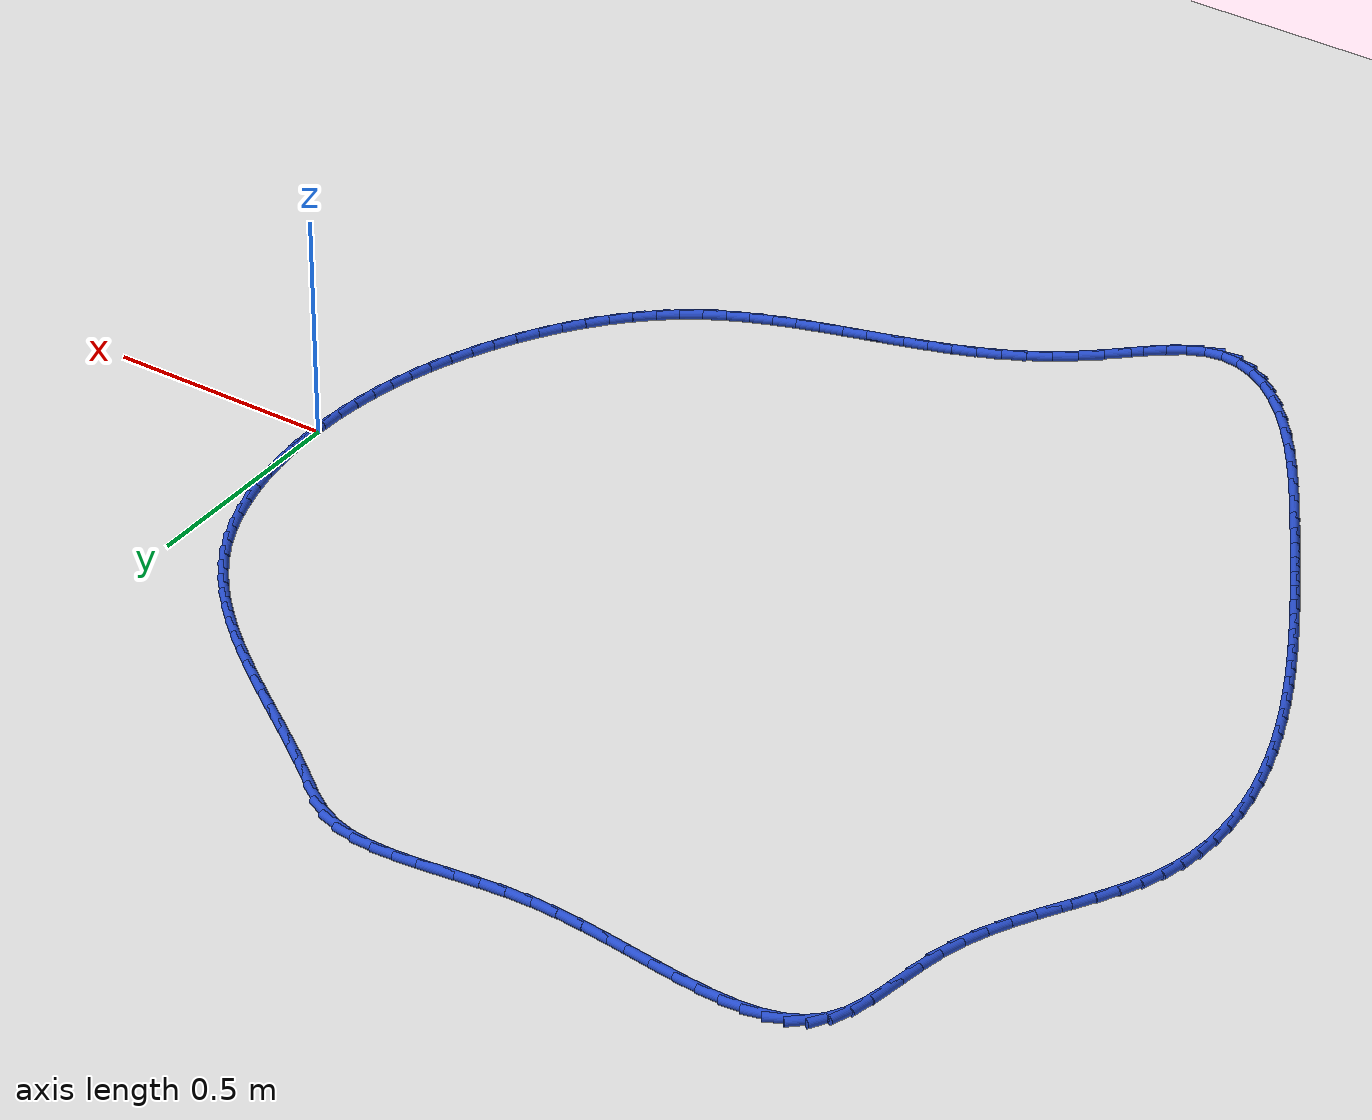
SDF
<sdf version="1.6">
 <world name="default">
  <light name="sun" type="directional">
   <pose>0 0 10 0 -0 0</pose>
   <diffuse>0.8 0.8 0.8 1</diffuse>
   <specular>0.2 0.2 0.2 1</specular>
   <attenuation>
    <range>1000</range>
    <constant>0.9</constant>
    <linear>0.01</linear>
    <quadratic>0.001</quadratic>
   </attenuation>
   <direction>-0.5 0.1 -0.9</direction>
  </light>
  <model name="ground_plane">
   <static>1</static>
   <link name="link">
    <collision name="collision">
     <geometry><plane><normal>0 0 1</normal><size>100 100</size></plane></geometry>
     <surface><friction><ode><mu>100</mu><mu2>50</mu2></ode></friction></surface>
    </collision>
    <visual name="visual">
     <cast_shadows>0</cast_shadows>
     <geometry><plane><normal>0 0 1</normal><size>100 100</size></plane></geometry>
     <material>
      <script><uri>file://media/materials/scripts/gazebo.material</uri><name>Gazebo/WhiteGlow</name></script>
     </material>
    </visual>
   </link>
  </model>
  <gravity>0 0 -9.8</gravity>
  <magnetic_field>6e-06 2.3e-05 -4.2e-05</magnetic_field>
  <atmosphere type="adiabatic"/>
  <physics name="default_physics" default="0" type="ode">
   <max_step_size>0.001</max_step_size>
   <real_time_factor>1</real_time_factor>
   <real_time_update_rate>1000</real_time_update_rate>
  </physics>
  <scene><ambient>0.4 0.4 0.4 1</ambient><background>0.7 0.7 0.7 1</background><shadows>1</shadows></scene>
  <spherical_coordinates>
   <surface_model>EARTH_WGS84</surface_model>
   <latitude_deg>0</latitude_deg>
   <longitude_deg>0</longitude_deg>
   <elevation>0</elevation>
   <heading_deg>0</heading_deg>
  </spherical_coordinates>
  <model name="line">
   <link name="link_0">
    <pose>5.551115123125783e-17 8.326672684688674e-17 0.01 0 1.57 -1.5558420849791224</pose>
    <collision name="collision">
     <geometry><cylinder><radius>0.01</radius><length>0.08</length></cylinder></geometry>
    </collision>
    <visual name="visual">
     <material>
      <script><name>Gazebo/Blue</name><uri>file://media/materials/scripts/gazebo.material</uri></script>
     </material>
     <geometry><cylinder><radius>0.01</radius><length>0.08</length></cylinder></geometry>
    </visual>
   </link>
   <link name="link_1">
    <pose>-0.0007722326352914149 0.05163585551971858 0.01 0 1.57 -1.5063671672619579</pose>
    <collision name="collision">
     <geometry><cylinder><radius>0.01</radius><length>0.08</length></cylinder></geometry>
    </collision>
    <visual name="visual">
     <material>
      <script><name>Gazebo/Blue</name><uri>file://media/materials/scripts/gazebo.material</uri></script>
     </material>
     <geometry><cylinder><radius>0.01</radius><length>0.08</length></cylinder></geometry>
    </visual>
   </link>
   <link name="link_2">
    <pose>-0.004109959740773728 0.10336875750954569 0.01 0 1.57 -1.4556124186254047</pose>
    <collision name="collision">
     <geometry><cylinder><radius>0.01</radius><length>0.08</length></cylinder></geometry>
    </collision>
    <visual name="visual">
     <material>
      <script><name>Gazebo/Blue</name><uri>file://media/materials/scripts/gazebo.material</uri></script>
     </material>
     <geometry><cylinder><radius>0.01</radius><length>0.08</length></cylinder></geometry>
    </visual>
   </link>
   <link name="link_3">
    <pose>-0.010072090712335637 0.15490148046679625 0.01 0 1.57 -1.4029882069615507</pose>
    <collision name="collision">
     <geometry><cylinder><radius>0.01</radius><length>0.08</length></cylinder></geometry>
    </collision>
    <visual name="visual">
     <material>
      <script><name>Gazebo/Blue</name><uri>file://media/materials/scripts/gazebo.material</uri></script>
     </material>
     <geometry><cylinder><radius>0.01</radius><length>0.08</length></cylinder></geometry>
    </visual>
   </link>
   <link name="link_4">
    <pose>-0.018717534945865894 0.205936798888785 0.01 0 1.57 -1.3479003062743522</pose>
    <collision name="collision">
     <geometry><cylinder><radius>0.01</radius><length>0.08</length></cylinder></geometry>
    </collision>
    <visual name="visual">
     <material>
      <script><name>Gazebo/Blue</name><uri>file://media/materials/scripts/gazebo.material</uri></script>
     </material>
     <geometry><cylinder><radius>0.01</radius><length>0.08</length></cylinder></geometry>
    </visual>
   </link>
   <link name="link_5">
    <pose>-0.030105201837253272 0.2561774872728268 0.01 0 1.57 -1.2897472828954946</pose>
    <collision name="collision">
     <geometry><cylinder><radius>0.01</radius><length>0.08</length></cylinder></geometry>
    </collision>
    <visual name="visual">
     <material>
      <script><name>Gazebo/Blue</name><uri>file://media/materials/scripts/gazebo.material</uri></script>
     </material>
     <geometry><cylinder><radius>0.01</radius><length>0.08</length></cylinder></geometry>
    </visual>
   </link>
   <link name="link_6">
    <pose>-0.04429400078238653 0.30532632011623645 0.01 0 1.57 -1.2279249217404302</pose>
    <collision name="collision">
     <geometry><cylinder><radius>0.01</radius><length>0.08</length></cylinder></geometry>
    </collision>
    <visual name="visual">
     <material>
      <script><name>Gazebo/Blue</name><uri>file://media/materials/scripts/gazebo.material</uri></script>
     </material>
     <geometry><cylinder><radius>0.01</radius><length>0.08</length></cylinder></geometry>
    </visual>
   </link>
   <link name="link_7">
    <pose>-0.0613428411771544 0.35308607191632857 0.01 0 1.57 -1.1618404105958577</pose>
    <collision name="collision">
     <geometry><cylinder><radius>0.01</radius><length>0.08</length></cylinder></geometry>
    </collision>
    <visual name="visual">
     <material>
      <script><name>Gazebo/Blue</name><uri>file://media/materials/scripts/gazebo.material</uri></script>
     </material>
     <geometry><cylinder><radius>0.01</radius><length>0.08</length></cylinder></geometry>
    </visual>
   </link>
   <link name="link_8">
    <pose>-0.08131063241744568 0.3991595171704182 0.01 0 1.57 -1.090956532182371</pose>
    <collision name="collision">
     <geometry><cylinder><radius>0.01</radius><length>0.08</length></cylinder></geometry>
    </collision>
    <visual name="visual">
     <material>
      <script><name>Gazebo/Blue</name><uri>file://media/materials/scripts/gazebo.material</uri></script>
     </material>
     <geometry><cylinder><radius>0.01</radius><length>0.08</length></cylinder></geometry>
    </visual>
   </link>
   <link name="link_9">
    <pose>-0.10425577282244455 0.4432502578206711 0.01 0 1.57 -1.0178648782062596</pose>
    <collision name="collision">
     <geometry><cylinder><radius>0.01</radius><length>0.08</length></cylinder></geometry>
    </collision>
    <visual name="visual">
     <material>
      <script><name>Gazebo/Blue</name><uri>file://media/materials/scripts/gazebo.material</uri></script>
     </material>
     <geometry><cylinder><radius>0.01</radius><length>0.08</length></cylinder></geometry>
    </visual>
   </link>
   <link name="link_10">
    <pose>-0.13014811983562152 0.485205245508208 0.01 0 1.57 -0.9493931200742121</pose>
    <collision name="collision">
     <geometry><cylinder><radius>0.01</radius><length>0.08</length></cylinder></geometry>
    </collision>
    <visual name="visual">
     <material>
      <script><name>Gazebo/Blue</name><uri>file://media/materials/scripts/gazebo.material</uri></script>
     </material>
     <geometry><cylinder><radius>0.01</radius><length>0.08</length></cylinder></geometry>
    </visual>
   </link>
   <link name="link_11">
    <pose>-0.15876892475239887 0.5251767895332603 0.01 0 1.57 -0.8871335537984706</pose>
    <collision name="collision">
     <geometry><cylinder><radius>0.01</radius><length>0.08</length></cylinder></geometry>
    </collision>
    <visual name="visual">
     <material>
      <script><name>Gazebo/Blue</name><uri>file://media/materials/scripts/gazebo.material</uri></script>
     </material>
     <geometry><cylinder><radius>0.01</radius><length>0.08</length></cylinder></geometry>
    </visual>
   </link>
   <link name="link_12">
    <pose>-0.18987524967512165 0.5633563620518326 0.01 0 1.57 -0.8315581066249936</pose>
    <collision name="collision">
     <geometry><cylinder><radius>0.01</radius><length>0.08</length></cylinder></geometry>
    </collision>
    <visual name="visual">
     <material>
      <script><name>Gazebo/Blue</name><uri>file://media/materials/scripts/gazebo.material</uri></script>
     </material>
     <geometry><cylinder><radius>0.01</radius><length>0.08</length></cylinder></geometry>
    </visual>
   </link>
   <link name="link_13">
    <pose>-0.22322415670613488 0.5999354352199295 0.01 0 1.57 -0.7828668469247678</pose>
    <collision name="collision">
     <geometry><cylinder><radius>0.01</radius><length>0.08</length></cylinder></geometry>
    </collision>
    <visual name="visual">
     <material>
      <script><name>Gazebo/Blue</name><uri>file://media/materials/scripts/gazebo.material</uri></script>
     </material>
     <geometry><cylinder><radius>0.01</radius><length>0.08</length></cylinder></geometry>
    </visual>
   </link>
   <link name="link_14">
    <pose>-0.25857270794778336 0.6351054811935553 0.01 0 1.57 -0.741058168596221</pose>
    <collision name="collision">
     <geometry><cylinder><radius>0.01</radius><length>0.08</length></cylinder></geometry>
    </collision>
    <visual name="visual">
     <material>
      <script><name>Gazebo/Blue</name><uri>file://media/materials/scripts/gazebo.material</uri></script>
     </material>
     <geometry><cylinder><radius>0.01</radius><length>0.08</length></cylinder></geometry>
    </visual>
   </link>
   <link name="link_15">
    <pose>-0.2956779655024125 0.669057972128715 0.01 0 1.57 -0.7059989615642379</pose>
    <collision name="collision">
     <geometry><cylinder><radius>0.01</radius><length>0.08</length></cylinder></geometry>
    </collision>
    <visual name="visual">
     <material>
      <script><name>Gazebo/Blue</name><uri>file://media/materials/scripts/gazebo.material</uri></script>
     </material>
     <geometry><cylinder><radius>0.01</radius><length>0.08</length></cylinder></geometry>
    </visual>
   </link>
   <link name="link_16">
    <pose>-0.3342969914723668 0.701984380181413 0.01 0 1.57 -0.6774850338123963</pose>
    <collision name="collision">
     <geometry><cylinder><radius>0.01</radius><length>0.08</length></cylinder></geometry>
    </collision>
    <visual name="visual">
     <material>
      <script><name>Gazebo/Blue</name><uri>file://media/materials/scripts/gazebo.material</uri></script>
     </material>
     <geometry><cylinder><radius>0.01</radius><length>0.08</length></cylinder></geometry>
    </visual>
   </link>
   <link name="link_17">
    <pose>-0.37418684795999163 0.7340761775076537 0.01 0 1.57 -0.6552881118612386</pose>
    <collision name="collision">
     <geometry><cylinder><radius>0.01</radius><length>0.08</length></cylinder></geometry>
    </collision>
    <visual name="visual">
     <material>
      <script><name>Gazebo/Blue</name><uri>file://media/materials/scripts/gazebo.material</uri></script>
     </material>
     <geometry><cylinder><radius>0.01</radius><length>0.08</length></cylinder></geometry>
    </visual>
   </link>
   <link name="link_18">
    <pose>-0.4151045970676317 0.7655248362634419 0.01 0 1.57 -0.6391896097318547</pose>
    <collision name="collision">
     <geometry><cylinder><radius>0.01</radius><length>0.08</length></cylinder></geometry>
    </collision>
    <visual name="visual">
     <material>
      <script><name>Gazebo/Blue</name><uri>file://media/materials/scripts/gazebo.material</uri></script>
     </material>
     <geometry><cylinder><radius>0.01</radius><length>0.08</length></cylinder></geometry>
    </visual>
   </link>
   <link name="link_19">
    <pose>-0.4568073008976322 0.7965218286047822 0.01 0 1.57 -0.6290031770769404</pose>
    <collision name="collision">
     <geometry><cylinder><radius>0.01</radius><length>0.08</length></cylinder></geometry>
    </collision>
    <visual name="visual">
     <material>
      <script><name>Gazebo/Blue</name><uri>file://media/materials/scripts/gazebo.material</uri></script>
     </material>
     <geometry><cylinder><radius>0.01</radius><length>0.08</length></cylinder></geometry>
    </visual>
   </link>
   <link name="link_20">
    <pose>-0.4990520215523381 0.8272586266876789 0.01 0 1.57 -0.6245884747594281</pose>
    <collision name="collision">
     <geometry><cylinder><radius>0.01</radius><length>0.08</length></cylinder></geometry>
    </collision>
    <visual name="visual">
     <material>
      <script><name>Gazebo/Blue</name><uri>file://media/materials/scripts/gazebo.material</uri></script>
     </material>
     <geometry><cylinder><radius>0.01</radius><length>0.08</length></cylinder></geometry>
    </visual>
   </link>
   <link name="link_21">
    <pose>-0.5415958211340943 0.8579267026681368 0.01 0 1.57 -0.6258583143683455</pose>
    <collision name="collision">
     <geometry><cylinder><radius>0.01</radius><length>0.08</length></cylinder></geometry>
    </collision>
    <visual name="visual">
     <material>
      <script><name>Gazebo/Blue</name><uri>file://media/materials/scripts/gazebo.material</uri></script>
     </material>
     <geometry><cylinder><radius>0.01</radius><length>0.08</length></cylinder></geometry>
    </visual>
   </link>
   <link name="link_22">
    <pose>-0.5841957617452458 0.8887175287021603 0.01 0 1.57 -0.6327806665517949</pose>
    <collision name="collision">
     <geometry><cylinder><radius>0.01</radius><length>0.08</length></cylinder></geometry>
    </collision>
    <visual name="visual">
     <material>
      <script><name>Gazebo/Blue</name><uri>file://media/materials/scripts/gazebo.material</uri></script>
     </material>
     <geometry><cylinder><radius>0.01</radius><length>0.08</length></cylinder></geometry>
    </visual>
   </link>
   <link name="link_23">
    <pose>-0.6266089054881376 0.9198225769457542 0.01 0 1.57 -0.6453763254640165</pose>
    <collision name="collision">
     <geometry><cylinder><radius>0.01</radius><length>0.08</length></cylinder></geometry>
    </collision>
    <visual name="visual">
     <material>
      <script><name>Gazebo/Blue</name><uri>file://media/materials/scripts/gazebo.material</uri></script>
     </material>
     <geometry><cylinder><radius>0.01</radius><length>0.08</length></cylinder></geometry>
    </visual>
   </link>
   <link name="link_24">
    <pose>-0.6685923144651147 0.9514333195549228 0.01 0 1.57 -0.6636748674826974</pose>
    <collision name="collision">
     <geometry><cylinder><radius>0.01</radius><length>0.08</length></cylinder></geometry>
    </collision>
    <visual name="visual">
     <material>
      <script><name>Gazebo/Blue</name><uri>file://media/materials/scripts/gazebo.material</uri></script>
     </material>
     <geometry><cylinder><radius>0.01</radius><length>0.08</length></cylinder></geometry>
    </visual>
   </link>
   <link name="link_25">
    <pose>-0.7099036691464841 0.9837392188281807 0.01 0 1.57 -0.6671351583942463</pose>
    <collision name="collision">
     <geometry><cylinder><radius>0.01</radius><length>0.08</length></cylinder></geometry>
    </collision>
    <visual name="visual">
     <material>
      <script><name>Gazebo/Blue</name><uri>file://media/materials/scripts/gazebo.material</uri></script>
     </material>
     <geometry><cylinder><radius>0.01</radius><length>0.08</length></cylinder></geometry>
    </visual>
   </link>
   <link name="link_26">
    <pose>-0.7506408762146539 1.0158239129545878 0.01 0 1.57 -0.5974731530288941</pose>
    <collision name="collision">
     <geometry><cylinder><radius>0.01</radius><length>0.08</length></cylinder></geometry>
    </collision>
    <visual name="visual">
     <material>
      <script><name>Gazebo/Blue</name><uri>file://media/materials/scripts/gazebo.material</uri></script>
     </material>
     <geometry><cylinder><radius>0.01</radius><length>0.08</length></cylinder></geometry>
    </visual>
   </link>
   <link name="link_27">
    <pose>-0.7918055526931449 1.0438337453245659 0.01 0 1.57 -0.44142695521278325</pose>
    <collision name="collision">
     <geometry><cylinder><radius>0.01</radius><length>0.08</length></cylinder></geometry>
    </collision>
    <visual name="visual">
     <material>
      <script><name>Gazebo/Blue</name><uri>file://media/materials/scripts/gazebo.material</uri></script>
     </material>
     <geometry><cylinder><radius>0.01</radius><length>0.08</length></cylinder></geometry>
    </visual>
   </link>
   <link name="link_28">
    <pose>-0.8344394997565895 1.0639793476541815 0.01 0 1.57 -0.26747660866811307</pose>
    <collision name="collision">
     <geometry><cylinder><radius>0.01</radius><length>0.08</length></cylinder></geometry>
    </collision>
    <visual name="visual">
     <material>
      <script><name>Gazebo/Blue</name><uri>file://media/materials/scripts/gazebo.material</uri></script>
     </material>
     <geometry><cylinder><radius>0.01</radius><length>0.08</length></cylinder></geometry>
    </visual>
   </link>
   <link name="link_29">
    <pose>-0.8788560352390451 1.076151404071915 0.01 0 1.57 -0.12075955600595661</pose>
    <collision name="collision">
     <geometry><cylinder><radius>0.01</radius><length>0.08</length></cylinder></geometry>
    </collision>
    <visual name="visual">
     <material>
      <script><name>Gazebo/Blue</name><uri>file://media/materials/scripts/gazebo.material</uri></script>
     </material>
     <geometry><cylinder><radius>0.01</radius><length>0.08</length></cylinder></geometry>
    </visual>
   </link>
   <link name="link_30">
    <pose>-0.9250678609733516 1.0817592094676391 0.01 0 1.57 -0.00952965241427522</pose>
    <collision name="collision">
     <geometry><cylinder><radius>0.01</radius><length>0.08</length></cylinder></geometry>
    </collision>
    <visual name="visual">
     <material>
      <script><name>Gazebo/Blue</name><uri>file://media/materials/scripts/gazebo.material</uri></script>
     </material>
     <geometry><cylinder><radius>0.01</radius><length>0.08</length></cylinder></geometry>
    </visual>
   </link>
   <link name="link_31">
    <pose>-0.9730867349907076 1.082216826499153 0.01 0 1.57 0.06568908597823814</pose>
    <collision name="collision">
     <geometry><cylinder><radius>0.01</radius><length>0.08</length></cylinder></geometry>
    </collision>
    <visual name="visual">
     <material>
      <script><name>Gazebo/Blue</name><uri>file://media/materials/scripts/gazebo.material</uri></script>
     </material>
     <geometry><cylinder><radius>0.01</radius><length>0.08</length></cylinder></geometry>
    </visual>
   </link>
   <link name="link_32">
    <pose>-1.022924415322312 1.078938317824256 0.01 0 1.57 0.1079732932506022</pose>
    <collision name="collision">
     <geometry><cylinder><radius>0.01</radius><length>0.08</length></cylinder></geometry>
    </collision>
    <visual name="visual">
     <material>
      <script><name>Gazebo/Blue</name><uri>file://media/materials/scripts/gazebo.material</uri></script>
     </material>
     <geometry><cylinder><radius>0.01</radius><length>0.08</length></cylinder></geometry>
    </visual>
   </link>
   <link name="link_33">
    <pose>-1.0745926599993632 1.073337746100746 0.01 0 1.57 0.12103698324139515</pose>
    <collision name="collision">
     <geometry><cylinder><radius>0.01</radius><length>0.08</length></cylinder></geometry>
    </collision>
    <visual name="visual">
     <material>
      <script><name>Gazebo/Blue</name><uri>file://media/materials/scripts/gazebo.material</uri></script>
     </material>
     <geometry><cylinder><radius>0.01</radius><length>0.08</length></cylinder></geometry>
    </visual>
   </link>
   <link name="link_34">
    <pose>-1.1281032270530598 1.0668291739864222 0.01 0 1.57 0.10799591371574249</pose>
    <collision name="collision">
     <geometry><cylinder><radius>0.01</radius><length>0.08</length></cylinder></geometry>
    </collision>
    <visual name="visual">
     <material>
      <script><name>Gazebo/Blue</name><uri>file://media/materials/scripts/gazebo.material</uri></script>
     </material>
     <geometry><cylinder><radius>0.01</radius><length>0.08</length></cylinder></geometry>
    </visual>
   </link>
   <link name="link_35">
    <pose>-1.183467874514601 1.0608266641390838 0.01 0 1.57 0.07121172890424289</pose>
    <collision name="collision">
     <geometry><cylinder><radius>0.01</radius><length>0.08</length></cylinder></geometry>
    </collision>
    <visual name="visual">
     <material>
      <script><name>Gazebo/Blue</name><uri>file://media/materials/scripts/gazebo.material</uri></script>
     </material>
     <geometry><cylinder><radius>0.01</radius><length>0.08</length></cylinder></geometry>
    </visual>
   </link>
   <link name="link_36">
    <pose>-1.2406983604151853 1.0567442792165291 0.01 0 1.57 0.01288337713004159</pose>
    <collision name="collision">
     <geometry><cylinder><radius>0.01</radius><length>0.08</length></cylinder></geometry>
    </collision>
    <visual name="visual">
     <material>
      <script><name>Gazebo/Blue</name><uri>file://media/materials/scripts/gazebo.material</uri></script>
     </material>
     <geometry><cylinder><radius>0.01</radius><length>0.08</length></cylinder></geometry>
    </visual>
   </link>
   <link name="link_37">
    <pose>-1.299802297958043 1.0559827787671894 0.01 0 1.57 -0.050339240659916615</pose>
    <collision name="collision">
     <geometry><cylinder><radius>0.01</radius><length>0.08</length></cylinder></geometry>
    </collision>
    <visual name="visual">
     <material>
      <script><name>Gazebo/Blue</name><uri>file://media/materials/scripts/gazebo.material</uri></script>
     </material>
     <geometry><cylinder><radius>0.01</radius><length>0.08</length></cylinder></geometry>
    </visual>
   </link>
   <link name="link_38">
    <pose>-1.360506339075548 1.0590411578893697 0.01 0 1.57 -0.09579042090000613</pose>
    <collision name="collision">
     <geometry><cylinder><radius>0.01</radius><length>0.08</length></cylinder></geometry>
    </collision>
    <visual name="visual">
     <material>
      <script><name>Gazebo/Blue</name><uri>file://media/materials/scripts/gazebo.material</uri></script>
     </material>
     <geometry><cylinder><radius>0.01</radius><length>0.08</length></cylinder></geometry>
    </visual>
   </link>
   <link name="link_39">
    <pose>-1.4220820003503705 1.0649576235908578 0.01 0 1.57 -0.12387242446322284</pose>
    <collision name="collision">
     <geometry><cylinder><radius>0.01</radius><length>0.08</length></cylinder></geometry>
    </collision>
    <visual name="visual">
     <material>
      <script><name>Gazebo/Blue</name><uri>file://media/materials/scripts/gazebo.material</uri></script>
     </material>
     <geometry><cylinder><radius>0.01</radius><length>0.08</length></cylinder></geometry>
    </visual>
   </link>
   <link name="link_40">
    <pose>-1.4837592572646294 1.0726370538708583 0.01 0 1.57 -0.13597644317732396</pose>
    <collision name="collision">
     <geometry><cylinder><radius>0.01</radius><length>0.08</length></cylinder></geometry>
    </collision>
    <visual name="visual">
     <material>
      <script><name>Gazebo/Blue</name><uri>file://media/materials/scripts/gazebo.material</uri></script>
     </material>
     <geometry><cylinder><radius>0.01</radius><length>0.08</length></cylinder></geometry>
    </visual>
   </link>
   <link name="link_41">
    <pose>-1.5447680853004475 1.080984326728577 0.01 0 1.57 -0.13217672540186018</pose>
    <collision name="collision">
     <geometry><cylinder><radius>0.01</radius><length>0.08</length></cylinder></geometry>
    </collision>
    <visual name="visual">
     <material>
      <script><name>Gazebo/Blue</name><uri>file://media/materials/scripts/gazebo.material</uri></script>
     </material>
     <geometry><cylinder><radius>0.01</radius><length>0.08</length></cylinder></geometry>
    </visual>
   </link>
   <link name="link_42">
    <pose>-1.604338459939943 1.088904320163218 0.01 0 1.57 -0.11107132129537188</pose>
    <collision name="collision">
     <geometry><cylinder><radius>0.01</radius><length>0.08</length></cylinder></geometry>
    </collision>
    <visual name="visual">
     <material>
      <script><name>Gazebo/Blue</name><uri>file://media/materials/scripts/gazebo.material</uri></script>
     </material>
     <geometry><cylinder><radius>0.01</radius><length>0.08</length></cylinder></geometry>
    </visual>
   </link>
   <link name="link_43">
    <pose>-1.6617003566652382 1.0953019121739862 0.01 0 1.57 -0.069396157308647</pose>
    <collision name="collision">
     <geometry><cylinder><radius>0.01</radius><length>0.08</length></cylinder></geometry>
    </collision>
    <visual name="visual">
     <material>
      <script><name>Gazebo/Blue</name><uri>file://media/materials/scripts/gazebo.material</uri></script>
     </material>
     <geometry><cylinder><radius>0.01</radius><length>0.08</length></cylinder></geometry>
    </visual>
   </link>
   <link name="link_44">
    <pose>-1.7160837509584534 1.099081980760087 0.01 0 1.57 -0.0013315551975847824</pose>
    <collision name="collision">
     <geometry><cylinder><radius>0.01</radius><length>0.08</length></cylinder></geometry>
    </collision>
    <visual name="visual">
     <material>
      <script><name>Gazebo/Blue</name><uri>file://media/materials/scripts/gazebo.material</uri></script>
     </material>
     <geometry><cylinder><radius>0.01</radius><length>0.08</length></cylinder></geometry>
    </visual>
   </link>
   <link name="link_45">
    <pose>-1.7667186183017092 1.0991494039207248 0.01 0 1.57 0.10243129217494552</pose>
    <collision name="collision">
     <geometry><cylinder><radius>0.01</radius><length>0.08</length></cylinder></geometry>
    </collision>
    <visual name="visual">
     <material>
      <script><name>Gazebo/Blue</name><uri>file://media/materials/scripts/gazebo.material</uri></script>
     </material>
     <geometry><cylinder><radius>0.01</radius><length>0.08</length></cylinder></geometry>
    </visual>
   </link>
   <link name="link_46">
    <pose>-1.8128349341771264 1.0944090596551046 0.01 0 1.57 0.2550108233182628</pose>
    <collision name="collision">
     <geometry><cylinder><radius>0.01</radius><length>0.08</length></cylinder></geometry>
    </collision>
    <visual name="visual">
     <material>
      <script><name>Gazebo/Blue</name><uri>file://media/materials/scripts/gazebo.material</uri></script>
     </material>
     <geometry><cylinder><radius>0.01</radius><length>0.08</length></cylinder></geometry>
    </visual>
   </link>
   <link name="link_47">
    <pose>-1.8536626740668247 1.0837658259624317 0.01 0 1.57 0.46953597474189485</pose>
    <collision name="collision">
     <geometry><cylinder><radius>0.01</radius><length>0.08</length></cylinder></geometry>
    </collision>
    <visual name="visual">
     <material>
      <script><name>Gazebo/Blue</name><uri>file://media/materials/scripts/gazebo.material</uri></script>
     </material>
     <geometry><cylinder><radius>0.01</radius><length>0.08</length></cylinder></geometry>
    </visual>
   </link>
   <link name="link_48">
    <pose>-1.8884318134529265 1.0661245808419104 0.01 0 1.57 0.7443194646886515</pose>
    <collision name="collision">
     <geometry><cylinder><radius>0.01</radius><length>0.08</length></cylinder></geometry>
    </collision>
    <visual name="visual">
     <material>
      <script><name>Gazebo/Blue</name><uri>file://media/materials/scripts/gazebo.material</uri></script>
     </material>
     <geometry><cylinder><radius>0.01</radius><length>0.08</length></cylinder></geometry>
    </visual>
   </link>
   <link name="link_49">
    <pose>-1.9163723278175506 1.0403902022927458 0.01 0 1.57 1.0400190390318254</pose>
    <collision name="collision">
     <geometry><cylinder><radius>0.01</radius><length>0.08</length></cylinder></geometry>
    </collision>
    <visual name="visual">
     <material>
      <script><name>Gazebo/Blue</name><uri>file://media/materials/scripts/gazebo.material</uri></script>
     </material>
     <geometry><cylinder><radius>0.01</radius><length>0.08</length></cylinder></geometry>
    </visual>
   </link>
   <link name="link_50">
    <pose>-1.9368100422857033 1.0055706947925813 0.01 0 1.57 1.2594655329003375</pose>
    <collision name="collision">
     <geometry><cylinder><radius>0.01</radius><length>0.08</length></cylinder></geometry>
    </collision>
    <visual name="visual">
     <material>
      <script><name>Gazebo/Blue</name><uri>file://media/materials/scripts/gazebo.material</uri></script>
     </material>
     <geometry><cylinder><radius>0.01</radius><length>0.08</length></cylinder></geometry>
    </visual>
   </link>
   <link name="link_51">
    <pose>-1.9506951701000377 0.9624217733075872 0.01 0 1.57 1.3775930186529721</pose>
    <collision name="collision">
     <geometry><cylinder><radius>0.01</radius><length>0.08</length></cylinder></geometry>
    </collision>
    <visual name="visual">
     <material>
      <script><name>Gazebo/Blue</name><uri>file://media/materials/scripts/gazebo.material</uri></script>
     </material>
     <geometry><cylinder><radius>0.01</radius><length>0.08</length></cylinder></geometry>
    </visual>
   </link>
   <link name="link_52">
    <pose>-1.9603334059727455 0.9131575414461399 0.01 0 1.57 1.4261354426066433</pose>
    <collision name="collision">
     <geometry><cylinder><radius>0.01</radius><length>0.08</length></cylinder></geometry>
    </collision>
    <visual name="visual">
     <material>
      <script><name>Gazebo/Blue</name><uri>file://media/materials/scripts/gazebo.material</uri></script>
     </material>
     <geometry><cylinder><radius>0.01</radius><length>0.08</length></cylinder></geometry>
    </visual>
   </link>
   <link name="link_53">
    <pose>-1.9680719601568946 0.8600367701873263 0.01 0 1.57 1.4222942179313471</pose>
    <collision name="collision">
     <geometry><cylinder><radius>0.01</radius><length>0.08</length></cylinder></geometry>
    </collision>
    <visual name="visual">
     <material>
      <script><name>Gazebo/Blue</name><uri>file://media/materials/scripts/gazebo.material</uri></script>
     </material>
     <geometry><cylinder><radius>0.01</radius><length>0.08</length></cylinder></geometry>
    </visual>
   </link>
   <link name="link_54">
    <pose>-1.9762580429055523 0.8053182305102313 0.01 0 1.57 1.3703909448817742</pose>
    <collision name="collision">
     <geometry><cylinder><radius>0.01</radius><length>0.08</length></cylinder></geometry>
    </collision>
    <visual name="visual">
     <material>
      <script><name>Gazebo/Blue</name><uri>file://media/materials/scripts/gazebo.material</uri></script>
     </material>
     <geometry><cylinder><radius>0.01</radius><length>0.08</length></cylinder></geometry>
    </visual>
   </link>
   <link name="link_55">
    <pose>-1.9872388644717864 0.7512606933939399 0.01 0 1.57 1.2761711292891407</pose>
    <collision name="collision">
     <geometry><cylinder><radius>0.01</radius><length>0.08</length></cylinder></geometry>
    </collision>
    <visual name="visual">
     <material>
      <script><name>Gazebo/Blue</name><uri>file://media/materials/scripts/gazebo.material</uri></script>
     </material>
     <geometry><cylinder><radius>0.01</radius><length>0.08</length></cylinder></geometry>
    </visual>
   </link>
   <link name="link_56">
    <pose>-2.0028746647941884 0.6997350811756554 0.01 0 1.57 1.185138527638121</pose>
    <collision name="collision">
     <geometry><cylinder><radius>0.01</radius><length>0.08</length></cylinder></geometry>
    </collision>
    <visual name="visual">
     <material>
      <script><name>Gazebo/Blue</name><uri>file://media/materials/scripts/gazebo.material</uri></script>
     </material>
     <geometry><cylinder><radius>0.01</radius><length>0.08</length></cylinder></geometry>
    </visual>
   </link>
   <link name="link_57">
    <pose>-2.022743793394732 0.6507948992521517 0.01 0 1.57 1.1140662660246965</pose>
    <collision name="collision">
     <geometry><cylinder><radius>0.01</radius><length>0.08</length></cylinder></geometry>
    </collision>
    <visual name="visual">
     <material>
      <script><name>Gazebo/Blue</name><uri>file://media/materials/scripts/gazebo.material</uri></script>
     </material>
     <geometry><cylinder><radius>0.01</radius><length>0.08</length></cylinder></geometry>
    </visual>
   </link>
   <link name="link_58">
    <pose>-2.0457567844491593 0.6039617699313085 0.01 0 1.57 1.0644811503852387</pose>
    <collision name="collision">
     <geometry><cylinder><radius>0.01</radius><length>0.08</length></cylinder></geometry>
    </collision>
    <visual name="visual">
     <material>
      <script><name>Gazebo/Blue</name><uri>file://media/materials/scripts/gazebo.material</uri></script>
     </material>
     <geometry><cylinder><radius>0.01</radius><length>0.08</length></cylinder></geometry>
    </visual>
   </link>
   <link name="link_59">
    <pose>-2.0708240884428486 0.5587572488656165 0.01 0 1.57 1.037089022154803</pose>
    <collision name="collision">
     <geometry><cylinder><radius>0.01</radius><length>0.08</length></cylinder></geometry>
    </collision>
    <visual name="visual">
     <material>
      <script><name>Gazebo/Blue</name><uri>file://media/materials/scripts/gazebo.material</uri></script>
     </material>
     <geometry><cylinder><radius>0.01</radius><length>0.08</length></cylinder></geometry>
    </visual>
   </link>
   <link name="link_60">
    <pose>-2.0968561558611767 0.5147028917075684 0.01 0 1.57 1.0324522934838463</pose>
    <collision name="collision">
     <geometry><cylinder><radius>0.01</radius><length>0.08</length></cylinder></geometry>
    </collision>
    <visual name="visual">
     <material>
      <script><name>Gazebo/Blue</name><uri>file://media/materials/scripts/gazebo.material</uri></script>
     </material>
     <geometry><cylinder><radius>0.01</radius><length>0.08</length></cylinder></geometry>
    </visual>
   </link>
   <link name="link_61">
    <pose>-2.122763437189521 0.4713202541096551 0.01 0 1.57 1.0514179234783891</pose>
    <collision name="collision">
     <geometry><cylinder><radius>0.01</radius><length>0.08</length></cylinder></geometry>
    </collision>
    <visual name="visual">
     <material>
      <script><name>Gazebo/Blue</name><uri>file://media/materials/scripts/gazebo.material</uri></script>
     </material>
     <geometry><cylinder><radius>0.01</radius><length>0.08</length></cylinder></geometry>
    </visual>
   </link>
   <link name="link_62">
    <pose>-2.1474563829132585 0.4281308917243688 0.01 0 1.57 1.0952267286158148</pose>
    <collision name="collision">
     <geometry><cylinder><radius>0.01</radius><length>0.08</length></cylinder></geometry>
    </collision>
    <visual name="visual">
     <material>
      <script><name>Gazebo/Blue</name><uri>file://media/materials/scripts/gazebo.material</uri></script>
     </material>
     <geometry><cylinder><radius>0.01</radius><length>0.08</length></cylinder></geometry>
    </visual>
   </link>
   <link name="link_63">
    <pose>-2.169845443517767 0.38465636020420046 0.01 0 1.57 1.165209206979345</pose>
    <collision name="collision">
     <geometry><cylinder><radius>0.01</radius><length>0.08</length></cylinder></geometry>
    </collision>
    <visual name="visual">
     <material>
      <script><name>Gazebo/Blue</name><uri>file://media/materials/scripts/gazebo.material</uri></script>
     </material>
     <geometry><cylinder><radius>0.01</radius><length>0.08</length></cylinder></geometry>
    </visual>
   </link>
   <link name="link_64">
    <pose>-2.188841069488423 0.34041821520164256 0.01 0 1.57 1.261082990423523</pose>
    <collision name="collision">
     <geometry><cylinder><radius>0.01</radius><length>0.08</length></cylinder></geometry>
    </collision>
    <visual name="visual">
     <material>
      <script><name>Gazebo/Blue</name><uri>file://media/materials/scripts/gazebo.material</uri></script>
     </material>
     <geometry><cylinder><radius>0.01</radius><length>0.08</length></cylinder></geometry>
    </visual>
   </link>
   <link name="link_65">
    <pose>-2.2033898366610196 0.29495494537095934 0.01 0 1.57 1.365408402615376</pose>
    <collision name="collision">
     <geometry><cylinder><radius>0.01</radius><length>0.08</length></cylinder></geometry>
    </collision>
    <visual name="visual">
     <material>
      <script><name>Gazebo/Blue</name><uri>file://media/materials/scripts/gazebo.material</uri></script>
     </material>
     <geometry><cylinder><radius>0.01</radius><length>0.08</length></cylinder></geometry>
    </visual>
   </link>
   <link name="link_66">
    <pose>-2.213143506373033 0.24813558030825936 0.01 0 1.57 1.461825110445225</pose>
    <collision name="collision">
     <geometry><cylinder><radius>0.01</radius><length>0.08</length></cylinder></geometry>
    </collision>
    <visual name="visual">
     <material>
      <script><name>Gazebo/Blue</name><uri>file://media/materials/scripts/gazebo.material</uri></script>
     </material>
     <geometry><cylinder><radius>0.01</radius><length>0.08</length></cylinder></geometry>
    </visual>
   </link>
   <link name="link_67">
    <pose>-2.2183955451956487 0.20012993550475164 0.01 0 1.57 1.5490237329471601</pose>
    <collision name="collision">
     <geometry><cylinder><radius>0.01</radius><length>0.08</length></cylinder></geometry>
    </collision>
    <visual name="visual">
     <material>
      <script><name>Gazebo/Blue</name><uri>file://media/materials/scripts/gazebo.material</uri></script>
     </material>
     <geometry><cylinder><radius>0.01</radius><length>0.08</length></cylinder></geometry>
    </visual>
   </link>
   <link name="link_68">
    <pose>-2.2194628135707424 0.1511187918388121 0.01 0 1.57 -1.5146580592736267</pose>
    <collision name="collision">
     <geometry><cylinder><radius>0.01</radius><length>0.08</length></cylinder></geometry>
    </collision>
    <visual name="visual">
     <material>
      <script><name>Gazebo/Blue</name><uri>file://media/materials/scripts/gazebo.material</uri></script>
     </material>
     <geometry><cylinder><radius>0.01</radius><length>0.08</length></cylinder></geometry>
    </visual>
   </link>
   <link name="link_69">
    <pose>-2.216662171940189 0.10128293018881818 0.01 0 1.57 -1.4456277320648403</pose>
    <collision name="collision">
     <geometry><cylinder><radius>0.01</radius><length>0.08</length></cylinder></geometry>
    </collision>
    <visual name="visual">
     <material>
      <script><name>Gazebo/Blue</name><uri>file://media/materials/scripts/gazebo.material</uri></script>
     </material>
     <geometry><cylinder><radius>0.01</radius><length>0.08</length></cylinder></geometry>
    </visual>
   </link>
   <link name="link_70">
    <pose>-2.210310480745865 0.050803131433145764 0.01 0 1.57 -1.384802262778311</pose>
    <collision name="collision">
     <geometry><cylinder><radius>0.01</radius><length>0.08</length></cylinder></geometry>
    </collision>
    <visual name="visual">
     <material>
      <script><name>Gazebo/Blue</name><uri>file://media/materials/scripts/gazebo.material</uri></script>
     </material>
     <geometry><cylinder><radius>0.01</radius><length>0.08</length></cylinder></geometry>
    </visual>
   </link>
   <link name="link_71">
    <pose>-2.2007246004296466 -0.00013982354982769452 0.01 0 1.57 -1.3313947405304896</pose>
    <collision name="collision">
     <geometry><cylinder><radius>0.01</radius><length>0.08</length></cylinder></geometry>
    </collision>
    <visual name="visual">
     <material>
      <script><name>Gazebo/Blue</name><uri>file://media/materials/scripts/gazebo.material</uri></script>
     </material>
     <geometry><cylinder><radius>0.01</radius><length>0.08</length></cylinder></geometry>
    </visual>
   </link>
   <link name="link_72">
    <pose>-2.188221391433408 -0.05136515388172594 0.01 0 1.57 -1.2846099919287695</pose>
    <collision name="collision">
     <geometry><cylinder><radius>0.01</radius><length>0.08</length></cylinder></geometry>
    </collision>
    <visual name="visual">
     <material>
      <script><name>Gazebo/Blue</name><uri>file://media/materials/scripts/gazebo.material</uri></script>
     </material>
     <geometry><cylinder><radius>0.01</radius><length>0.08</length></cylinder></geometry>
    </visual>
   </link>
   <link name="link_73">
    <pose>-2.173117714199025 -0.10269207868417317 0.01 0 1.57 -1.2437041880392112</pose>
    <collision name="collision">
     <geometry><cylinder><radius>0.01</radius><length>0.08</length></cylinder></geometry>
    </collision>
    <visual name="visual">
     <material>
      <script><name>Gazebo/Blue</name><uri>file://media/materials/scripts/gazebo.material</uri></script>
     </material>
     <geometry><cylinder><radius>0.01</radius><length>0.08</length></cylinder></geometry>
    </visual>
   </link>
   <link name="link_74">
    <pose>-2.155730429168374 -0.15393981707879092 0.01 0 1.57 -1.2080147572574191</pose>
    <collision name="collision">
     <geometry><cylinder><radius>0.01</radius><length>0.08</length></cylinder></geometry>
    </collision>
    <visual name="visual">
     <material>
      <script><name>Gazebo/Blue</name><uri>file://media/materials/scripts/gazebo.material</uri></script>
     </material>
     <geometry><cylinder><radius>0.01</radius><length>0.08</length></cylinder></geometry>
    </visual>
   </link>
   <link name="link_75">
    <pose>-2.1363763967833305 -0.20492758818720358 0.01 0 1.57 -1.176972180857771</pose>
    <collision name="collision">
     <geometry><cylinder><radius>0.01</radius><length>0.08</length></cylinder></geometry>
    </collision>
    <visual name="visual">
     <material>
      <script><name>Gazebo/Blue</name><uri>file://media/materials/scripts/gazebo.material</uri></script>
     </material>
     <geometry><cylinder><radius>0.01</radius><length>0.08</length></cylinder></geometry>
    </visual>
   </link>
   <link name="link_76">
    <pose>-2.1153724774857694 -0.2554746111310342 0.01 0 1.57 -1.1501019956360645</pose>
    <collision name="collision">
     <geometry><cylinder><radius>0.01</radius><length>0.08</length></cylinder></geometry>
    </collision>
    <visual name="visual">
     <material>
      <script><name>Gazebo/Blue</name><uri>file://media/materials/scripts/gazebo.material</uri></script>
     </material>
     <geometry><cylinder><radius>0.01</radius><length>0.08</length></cylinder></geometry>
    </visual>
   </link>
   <link name="link_77">
    <pose>-2.0930355317175673 -0.30540010503190645 0.01 0 1.57 -1.1270225048794114</pose>
    <collision name="collision">
     <geometry><cylinder><radius>0.01</radius><length>0.08</length></cylinder></geometry>
    </collision>
    <visual name="visual">
     <material>
      <script><name>Gazebo/Blue</name><uri>file://media/materials/scripts/gazebo.material</uri></script>
     </material>
     <geometry><cylinder><radius>0.01</radius><length>0.08</length></cylinder></geometry>
    </visual>
   </link>
   <link name="link_78">
    <pose>-2.0696824199205985 -0.35452328901144414 0.01 0 1.57 -1.1074417257570337</pose>
    <collision name="collision">
     <geometry><cylinder><radius>0.01</radius><length>0.08</length></cylinder></geometry>
    </collision>
    <visual name="visual">
     <material>
      <script><name>Gazebo/Blue</name><uri>file://media/materials/scripts/gazebo.material</uri></script>
     </material>
     <geometry><cylinder><radius>0.01</radius><length>0.08</length></cylinder></geometry>
    </visual>
   </link>
   <link name="link_79">
    <pose>-2.0456300025367398 -0.40266338219126924 0.01 0 1.57 -1.091155937896218</pose>
    <collision name="collision">
     <geometry><cylinder><radius>0.01</radius><length>0.08</length></cylinder></geometry>
    </collision>
    <visual name="visual">
     <material>
      <script><name>Gazebo/Blue</name><uri>file://media/materials/scripts/gazebo.material</uri></script>
     </material>
     <geometry><cylinder><radius>0.01</radius><length>0.08</length></cylinder></geometry>
    </visual>
   </link>
   <link name="link_80">
    <pose>-2.0211951400078667 -0.4496396036930057 0.01 0 1.57 -1.0780517042798528</pose>
    <collision name="collision">
     <geometry><cylinder><radius>0.01</radius><length>0.08</length></cylinder></geometry>
    </collision>
    <visual name="visual">
     <material>
      <script><name>Gazebo/Blue</name><uri>file://media/materials/scripts/gazebo.material</uri></script>
     </material>
     <geometry><cylinder><radius>0.01</radius><length>0.08</length></cylinder></geometry>
    </visual>
   </link>
   <link name="link_81">
    <pose>-1.9966946927758542 -0.4952711726382769 0.01 0 1.57 -1.0680801910807127</pose>
    <collision name="collision">
     <geometry><cylinder><radius>0.01</radius><length>0.08</length></cylinder></geometry>
    </collision>
    <visual name="visual">
     <material>
      <script><name>Gazebo/Blue</name><uri>file://media/materials/scripts/gazebo.material</uri></script>
     </material>
     <geometry><cylinder><radius>0.01</radius><length>0.08</length></cylinder></geometry>
    </visual>
   </link>
   <link name="link_82">
    <pose>-1.972437533715186 -0.5393883737828018 0.01 0 1.57 -1.0601422458499536</pose>
    <collision name="collision">
     <geometry><cylinder><radius>0.01</radius><length>0.08</length></cylinder></geometry>
    </collision>
    <visual name="visual">
     <material>
      <script><name>Gazebo/Blue</name><uri>file://media/materials/scripts/gazebo.material</uri></script>
     </material>
     <geometry><cylinder><radius>0.01</radius><length>0.08</length></cylinder></geometry>
    </visual>
   </link>
   <link name="link_83">
    <pose>-1.948434237698253 -0.582234741170904 0.01 0 1.57 -1.053047933606514</pose>
    <collision name="collision">
     <geometry><cylinder><radius>0.01</radius><length>0.08</length></cylinder></geometry>
    </collision>
    <visual name="visual">
     <material>
      <script><name>Gazebo/Blue</name><uri>file://media/materials/scripts/gazebo.material</uri></script>
     </material>
     <geometry><cylinder><radius>0.01</radius><length>0.08</length></cylinder></geometry>
    </visual>
   </link>
   <link name="link_84">
    <pose>-1.9243148040831006 -0.624581041880514 0.01 0 1.57 -1.047099280810003</pose>
    <collision name="collision">
     <geometry><cylinder><radius>0.01</radius><length>0.08</length></cylinder></geometry>
    </collision>
    <visual name="visual">
     <material>
      <script><name>Gazebo/Blue</name><uri>file://media/materials/scripts/gazebo.material</uri></script>
     </material>
     <geometry><cylinder><radius>0.01</radius><length>0.08</length></cylinder></geometry>
    </visual>
   </link>
   <link name="link_85">
    <pose>-1.8996844824667185 -0.6672323302495491 0.01 0 1.57 -1.0425766738360382</pose>
    <collision name="collision">
     <geometry><cylinder><radius>0.01</radius><length>0.08</length></cylinder></geometry>
    </collision>
    <visual name="visual">
     <material>
      <script><name>Gazebo/Blue</name><uri>file://media/materials/scripts/gazebo.material</uri></script>
     </material>
     <geometry><cylinder><radius>0.01</radius><length>0.08</length></cylinder></geometry>
    </visual>
   </link>
   <link name="link_86">
    <pose>-1.874148522446092 -0.7109936606159253 0.01 0 1.57 -1.0395951386382902</pose>
    <collision name="collision">
     <geometry><cylinder><radius>0.01</radius><length>0.08</length></cylinder></geometry>
    </collision>
    <visual name="visual">
     <material>
      <script><name>Gazebo/Blue</name><uri>file://media/materials/scripts/gazebo.material</uri></script>
     </material>
     <geometry><cylinder><radius>0.01</radius><length>0.08</length></cylinder></geometry>
    </visual>
   </link>
   <link name="link_87">
    <pose>-1.8473121736182099 -0.7566700873175607 0.01 0 1.57 -1.0380184008043578</pose>
    <collision name="collision">
     <geometry><cylinder><radius>0.01</radius><length>0.08</length></cylinder></geometry>
    </collision>
    <visual name="visual">
     <material>
      <script><name>Gazebo/Blue</name><uri>file://media/materials/scripts/gazebo.material</uri></script>
     </material>
     <geometry><cylinder><radius>0.01</radius><length>0.08</length></cylinder></geometry>
    </visual>
   </link>
   <link name="link_88">
    <pose>-1.8187862443146878 -0.805047433879199 0.01 0 1.57 -1.0342038536566205</pose>
    <collision name="collision">
     <geometry><cylinder><radius>0.01</radius><length>0.08</length></cylinder></geometry>
    </collision>
    <visual name="visual">
     <material>
      <script><name>Gazebo/Blue</name><uri>file://media/materials/scripts/gazebo.material</uri></script>
     </material>
     <geometry><cylinder><radius>0.01</radius><length>0.08</length></cylinder></geometry>
    </visual>
   </link>
   <link name="link_89">
    <pose>-1.7884126219289083 -0.8561120904001223 0.01 0 1.57 -1.0238552956262248</pose>
    <collision name="collision">
     <geometry><cylinder><radius>0.01</radius><length>0.08</length></cylinder></geometry>
    </collision>
    <visual name="visual">
     <material>
      <script><name>Gazebo/Blue</name><uri>file://media/materials/scripts/gazebo.material</uri></script>
     </material>
     <geometry><cylinder><radius>0.01</radius><length>0.08</length></cylinder></geometry>
    </visual>
   </link>
   <link name="link_90">
    <pose>-1.7563423413989065 -0.9087809304310257 0.01 0 1.57 -1.0068361174692921</pose>
    <collision name="collision">
     <geometry><cylinder><radius>0.01</radius><length>0.08</length></cylinder></geometry>
    </collision>
    <visual name="visual">
     <material>
      <script><name>Gazebo/Blue</name><uri>file://media/materials/scripts/gazebo.material</uri></script>
     </material>
     <geometry><cylinder><radius>0.01</radius><length>0.08</length></cylinder></geometry>
    </visual>
   </link>
   <link name="link_91">
    <pose>-1.7227480259134513 -0.9618961415294015 0.01 0 1.57 -0.9826631994743815</pose>
    <collision name="collision">
     <geometry><cylinder><radius>0.01</radius><length>0.08</length></cylinder></geometry>
    </collision>
    <visual name="visual">
     <material>
      <script><name>Gazebo/Blue</name><uri>file://media/materials/scripts/gazebo.material</uri></script>
     </material>
     <geometry><cylinder><radius>0.01</radius><length>0.08</length></cylinder></geometry>
    </visual>
   </link>
   <link name="link_92">
    <pose>-1.6878022986613157 -1.01429991125274 0.01 0 1.57 -0.95017437709596</pose>
    <collision name="collision">
     <geometry><cylinder><radius>0.01</radius><length>0.08</length></cylinder></geometry>
    </collision>
    <visual name="visual">
     <material>
      <script><name>Gazebo/Blue</name><uri>file://media/materials/scripts/gazebo.material</uri></script>
     </material>
     <geometry><cylinder><radius>0.01</radius><length>0.08</length></cylinder></geometry>
    </visual>
   </link>
   <link name="link_93">
    <pose>-1.65167778283127 -1.0648344271585333 0.01 0 1.57 -0.9073909421072486</pose>
    <collision name="collision">
     <geometry><cylinder><radius>0.01</radius><length>0.08</length></cylinder></geometry>
    </collision>
    <visual name="visual">
     <material>
      <script><name>Gazebo/Blue</name><uri>file://media/materials/scripts/gazebo.material</uri></script>
     </material>
     <geometry><cylinder><radius>0.01</radius><length>0.08</length></cylinder></geometry>
    </visual>
   </link>
   <link name="link_94">
    <pose>-1.6145471016120856 -1.1123418768042737 0.01 0 1.57 -0.8512219727040604</pose>
    <collision name="collision">
     <geometry><cylinder><radius>0.01</radius><length>0.08</length></cylinder></geometry>
    </collision>
    <visual name="visual">
     <material>
      <script><name>Gazebo/Blue</name><uri>file://media/materials/scripts/gazebo.material</uri></script>
     </material>
     <geometry><cylinder><radius>0.01</radius><length>0.08</length></cylinder></geometry>
    </visual>
   </link>
   <link name="link_95">
    <pose>-1.5765828781925315 -1.1556644477474525 0.01 0 1.57 -0.7769751207008078</pose>
    <collision name="collision">
     <geometry><cylinder><radius>0.01</radius><length>0.08</length></cylinder></geometry>
    </collision>
    <visual name="visual">
     <material>
      <script><name>Gazebo/Blue</name><uri>file://media/materials/scripts/gazebo.material</uri></script>
     </material>
     <geometry><cylinder><radius>0.01</radius><length>0.08</length></cylinder></geometry>
    </visual>
   </link>
   <link name="link_96">
    <pose>-1.5379577357613812 -1.193644327545561 0.01 0 1.57 -0.677674597674402</pose>
    <collision name="collision">
     <geometry><cylinder><radius>0.01</radius><length>0.08</length></cylinder></geometry>
    </collision>
    <visual name="visual">
     <material>
      <script><name>Gazebo/Blue</name><uri>file://media/materials/scripts/gazebo.material</uri></script>
     </material>
     <geometry><cylinder><radius>0.01</radius><length>0.08</length></cylinder></geometry>
    </visual>
   </link>
   <link name="link_97">
    <pose>-1.4988442975074039 -1.225123703756091 0.01 0 1.57 -0.5434646942765711</pose>
    <collision name="collision">
     <geometry><cylinder><radius>0.01</radius><length>0.08</length></cylinder></geometry>
    </collision>
    <visual name="visual">
     <material>
      <script><name>Gazebo/Blue</name><uri>file://media/materials/scripts/gazebo.material</uri></script>
     </material>
     <geometry><cylinder><radius>0.01</radius><length>0.08</length></cylinder></geometry>
    </visual>
   </link>
   <link name="link_98">
    <pose>-1.4594151866193716 -1.248944763936534 0.01 0 1.57 -0.3624293974409361</pose>
    <collision name="collision">
     <geometry><cylinder><radius>0.01</radius><length>0.08</length></cylinder></geometry>
    </collision>
    <visual name="visual">
     <material>
      <script><name>Gazebo/Blue</name><uri>file://media/materials/scripts/gazebo.material</uri></script>
     </material>
     <geometry><cylinder><radius>0.01</radius><length>0.08</length></cylinder></geometry>
    </visual>
   </link>
   <link name="link_99">
    <pose>-1.4198430262860549 -1.263949695644382 0.01 0 1.57 -0.12654976980469804</pose>
    <collision name="collision">
     <geometry><cylinder><radius>0.01</radius><length>0.08</length></cylinder></geometry>
    </collision>
    <visual name="visual">
     <material>
      <script><name>Gazebo/Blue</name><uri>file://media/materials/scripts/gazebo.material</uri></script>
     </material>
     <geometry><cylinder><radius>0.01</radius><length>0.08</length></cylinder></geometry>
    </visual>
   </link>
   <link name="link_100">
    <pose>-1.3803004396962237 -1.2689806864371262 0.01 0 1.57 0.15385082147564072</pose>
    <collision name="collision">
     <geometry><cylinder><radius>0.01</radius><length>0.08</length></cylinder></geometry>
    </collision>
    <visual name="visual">
     <material>
      <script><name>Gazebo/Blue</name><uri>file://media/materials/scripts/gazebo.material</uri></script>
     </material>
     <geometry><cylinder><radius>0.01</radius><length>0.08</length></cylinder></geometry>
    </visual>
   </link>
   <link name="link_101">
    <pose>-1.3409600500386507 -1.2628799238722583 0.01 0 1.57 0.43076382165456367</pose>
    <collision name="collision">
     <geometry><cylinder><radius>0.01</radius><length>0.08</length></cylinder></geometry>
    </collision>
    <visual name="visual">
     <material>
      <script><name>Gazebo/Blue</name><uri>file://media/materials/scripts/gazebo.material</uri></script>
     </material>
     <geometry><cylinder><radius>0.01</radius><length>0.08</length></cylinder></geometry>
    </visual>
   </link>
   <link name="link_102">
    <pose>-1.3019342308368886 -1.2449457715374748 0.01 0 1.57 0.6154410115260287</pose>
    <collision name="collision">
     <geometry><cylinder><radius>0.01</radius><length>0.08</length></cylinder></geometry>
    </collision>
    <visual name="visual">
     <material>
      <script><name>Gazebo/Blue</name><uri>file://media/materials/scripts/gazebo.material</uri></script>
     </material>
     <geometry><cylinder><radius>0.01</radius><length>0.08</length></cylinder></geometry>
    </visual>
   </link>
   <link name="link_103">
    <pose>-1.2629514815683571 -1.2173830679001014 0.01 0 1.57 0.7101916134764388</pose>
    <collision name="collision">
     <geometry><cylinder><radius>0.01</radius><length>0.08</length></cylinder></geometry>
    </collision>
    <visual name="visual">
     <material>
      <script><name>Gazebo/Blue</name><uri>file://media/materials/scripts/gazebo.material</uri></script>
     </material>
     <geometry><cylinder><radius>0.01</radius><length>0.08</length></cylinder></geometry>
    </visual>
   </link>
   <link name="link_104">
    <pose>-1.223589646594033 -1.1835373258644268 0.01 0 1.57 0.7414612388413875</pose>
    <collision name="collision">
     <geometry><cylinder><radius>0.01</radius><length>0.08</length></cylinder></geometry>
    </collision>
    <visual name="visual">
     <material>
      <script><name>Gazebo/Blue</name><uri>file://media/materials/scripts/gazebo.material</uri></script>
     </material>
     <geometry><cylinder><radius>0.01</radius><length>0.08</length></cylinder></geometry>
    </visual>
   </link>
   <link name="link_105">
    <pose>-1.1834262142977725 -1.146756753590038 0.01 0 1.57 0.7209212164480016</pose>
    <collision name="collision">
     <geometry><cylinder><radius>0.01</radius><length>0.08</length></cylinder></geometry>
    </collision>
    <visual name="visual">
     <material>
      <script><name>Gazebo/Blue</name><uri>file://media/materials/scripts/gazebo.material</uri></script>
     </material>
     <geometry><cylinder><radius>0.01</radius><length>0.08</length></cylinder></geometry>
    </visual>
   </link>
   <link name="link_106">
    <pose>-1.1420386730634327 -1.1103895592365216 0.01 0 1.57 0.6533499782347229</pose>
    <collision name="collision">
     <geometry><cylinder><radius>0.01</radius><length>0.08</length></cylinder></geometry>
    </collision>
    <visual name="visual">
     <material>
      <script><name>Gazebo/Blue</name><uri>file://media/materials/scripts/gazebo.material</uri></script>
     </material>
     <geometry><cylinder><radius>0.01</radius><length>0.08</length></cylinder></geometry>
    </visual>
   </link>
   <link name="link_107">
    <pose>-1.0990548995933431 -1.0774853138003 0.01 0 1.57 0.5737376530561025</pose>
    <collision name="collision">
     <geometry><cylinder><radius>0.01</radius><length>0.08</length></cylinder></geometry>
    </collision>
    <visual name="visual">
     <material>
      <script><name>Gazebo/Blue</name><uri>file://media/materials/scripts/gazebo.material</uri></script>
     </material>
     <geometry><cylinder><radius>0.01</radius><length>0.08</length></cylinder></geometry>
    </visual>
   </link>
   <link name="link_108">
    <pose>-1.054507274101149 -1.0486962115689753 0.01 0 1.57 0.5018234082398443</pose>
    <collision name="collision">
     <geometry><cylinder><radius>0.01</radius><length>0.08</length></cylinder></geometry>
    </collision>
    <visual name="visual">
     <material>
      <script><name>Gazebo/Blue</name><uri>file://media/materials/scripts/gazebo.material</uri></script>
     </material>
     <geometry><cylinder><radius>0.01</radius><length>0.08</length></cylinder></geometry>
    </visual>
   </link>
   <link name="link_109">
    <pose>-1.0086228472641567 -1.0235206906267338 0.01 0 1.57 0.43908540100056975</pose>
    <collision name="collision">
     <geometry><cylinder><radius>0.01</radius><length>0.08</length></cylinder></geometry>
    </collision>
    <visual name="visual">
     <material>
      <script><name>Gazebo/Blue</name><uri>file://media/materials/scripts/gazebo.material</uri></script>
     </material>
     <geometry><cylinder><radius>0.01</radius><length>0.08</length></cylinder></geometry>
    </visual>
   </link>
   <link name="link_110">
    <pose>-0.961629913874059 -1.0014498155473621 0.01 0 1.57 0.3863612829321901</pose>
    <collision name="collision">
     <geometry><cylinder><radius>0.01</radius><length>0.08</length></cylinder></geometry>
    </collision>
    <visual name="visual">
     <material>
      <script><name>Gazebo/Blue</name><uri>file://media/materials/scripts/gazebo.material</uri></script>
     </material>
     <geometry><cylinder><radius>0.01</radius><length>0.08</length></cylinder></geometry>
    </visual>
   </link>
   <link name="link_111">
    <pose>-0.9137567687225462 -0.9819746509046466 0.01 0 1.57 0.3440837754114941</pose>
    <collision name="collision">
     <geometry><cylinder><radius>0.01</radius><length>0.08</length></cylinder></geometry>
    </collision>
    <visual name="visual">
     <material>
      <script><name>Gazebo/Blue</name><uri>file://media/materials/scripts/gazebo.material</uri></script>
     </material>
     <geometry><cylinder><radius>0.01</radius><length>0.08</length></cylinder></geometry>
    </visual>
   </link>
   <link name="link_112">
    <pose>-0.8652317066013093 -0.9645862612723736 0.01 0 1.57 0.312424218156638</pose>
    <collision name="collision">
     <geometry><cylinder><radius>0.01</radius><length>0.08</length></cylinder></geometry>
    </collision>
    <visual name="visual">
     <material>
      <script><name>Gazebo/Blue</name><uri>file://media/materials/scripts/gazebo.material</uri></script>
     </material>
     <geometry><cylinder><radius>0.01</radius><length>0.08</length></cylinder></geometry>
    </visual>
   </link>
   <link name="link_113">
    <pose>-0.8162830223020392 -0.9487757112243298 0.01 0 1.57 0.2914277163134125</pose>
    <collision name="collision">
     <geometry><cylinder><radius>0.01</radius><length>0.08</length></cylinder></geometry>
    </collision>
    <visual name="visual">
     <material>
      <script><name>Gazebo/Blue</name><uri>file://media/materials/scripts/gazebo.material</uri></script>
     </material>
     <geometry><cylinder><radius>0.01</radius><length>0.08</length></cylinder></geometry>
    </visual>
   </link>
   <link name="link_114">
    <pose>-0.7671390106164283 -0.9340340653343018 0.01 0 1.57 0.2811202289246881</pose>
    <collision name="collision">
     <geometry><cylinder><radius>0.01</radius><length>0.08</length></cylinder></geometry>
    </collision>
    <visual name="visual">
     <material>
      <script><name>Gazebo/Blue</name><uri>file://media/materials/scripts/gazebo.material</uri></script>
     </material>
     <geometry><cylinder><radius>0.01</radius><length>0.08</length></cylinder></geometry>
    </visual>
   </link>
   <link name="link_115">
    <pose>-0.7180279663361673 -0.9198523881760762 0.01 0 1.57 0.28158141590123276</pose>
    <collision name="collision">
     <geometry><cylinder><radius>0.01</radius><length>0.08</length></cylinder></geometry>
    </collision>
    <visual name="visual">
     <material>
      <script><name>Gazebo/Blue</name><uri>file://media/materials/scripts/gazebo.material</uri></script>
     </material>
     <geometry><cylinder><radius>0.01</radius><length>0.08</length></cylinder></geometry>
    </visual>
   </link>
   <link name="link_116">
    <pose>-0.6691781842529471 -0.9057217443234392 0.01 0 1.57 0.29298283320987745</pose>
    <collision name="collision">
     <geometry><cylinder><radius>0.01</radius><length>0.08</length></cylinder></geometry>
    </collision>
    <visual name="visual">
     <material>
      <script><name>Gazebo/Blue</name><uri>file://media/materials/scripts/gazebo.material</uri></script>
     </material>
     <geometry><cylinder><radius>0.01</radius><length>0.08</length></cylinder></geometry>
    </visual>
   </link>
   <link name="link_117">
    <pose>-0.6208179591584585 -0.8911331983501775 0.01 0 1.57 0.3155908182385192</pose>
    <collision name="collision">
     <geometry><cylinder><radius>0.01</radius><length>0.08</length></cylinder></geometry>
    </collision>
    <visual name="visual">
     <material>
      <script><name>Gazebo/Blue</name><uri>file://media/materials/scripts/gazebo.material</uri></script>
     </material>
     <geometry><cylinder><radius>0.01</radius><length>0.08</length></cylinder></geometry>
    </visual>
   </link>
   <link name="link_118">
    <pose>-0.5731755858443944 -0.8755778148300781 0.01 0 1.57 0.34972980466737325</pose>
    <collision name="collision">
     <geometry><cylinder><radius>0.01</radius><length>0.08</length></cylinder></geometry>
    </collision>
    <visual name="visual">
     <material>
      <script><name>Gazebo/Blue</name><uri>file://media/materials/scripts/gazebo.material</uri></script>
     </material>
     <geometry><cylinder><radius>0.01</radius><length>0.08</length></cylinder></geometry>
    </visual>
   </link>
   <link name="link_119">
    <pose>-0.5264793591024447 -0.8585466583369273 0.01 0 1.57 0.39569773862249286</pose>
    <collision name="collision">
     <geometry><cylinder><radius>0.01</radius><length>0.08</length></cylinder></geometry>
    </collision>
    <visual name="visual">
     <material>
      <script><name>Gazebo/Blue</name><uri>file://media/materials/scripts/gazebo.material</uri></script>
     </material>
     <geometry><cylinder><radius>0.01</radius><length>0.08</length></cylinder></geometry>
    </visual>
   </link>
   <link name="link_120">
    <pose>-0.4809575737243011 -0.8395307934445115 0.01 0 1.57 0.45362465744123603</pose>
    <collision name="collision">
     <geometry><cylinder><radius>0.01</radius><length>0.08</length></cylinder></geometry>
    </collision>
    <visual name="visual">
     <material>
      <script><name>Gazebo/Blue</name><uri>file://media/materials/scripts/gazebo.material</uri></script>
     </material>
     <geometry><cylinder><radius>0.01</radius><length>0.08</length></cylinder></geometry>
    </visual>
   </link>
   <link name="link_121">
    <pose>-0.4368385245016546 -0.8180212847266172 0.01 0 1.57 0.5232742559506007</pose>
    <collision name="collision">
     <geometry><cylinder><radius>0.01</radius><length>0.08</length></cylinder></geometry>
    </collision>
    <visual name="visual">
     <material>
      <script><name>Gazebo/Blue</name><uri>file://media/materials/scripts/gazebo.material</uri></script>
     </material>
     <geometry><cylinder><radius>0.01</radius><length>0.08</length></cylinder></geometry>
    </visual>
   </link>
   <link name="link_122">
    <pose>-0.39435050622619583 -0.7935091967570308 0.01 0 1.57 0.603312921006417</pose>
    <collision name="collision">
     <geometry><cylinder><radius>0.01</radius><length>0.08</length></cylinder></geometry>
    </collision>
    <visual name="visual">
     <material>
      <script><name>Gazebo/Blue</name><uri>file://media/materials/scripts/gazebo.material</uri></script>
     </material>
     <geometry><cylinder><radius>0.01</radius><length>0.08</length></cylinder></geometry>
    </visual>
   </link>
   <link name="link_123">
    <pose>-0.35371624938489926 -0.7655117311550558 0.01 0 1.57 0.6840687314001356</pose>
    <collision name="collision">
     <geometry><cylinder><radius>0.01</radius><length>0.08</length></cylinder></geometry>
    </collision>
    <visual name="visual">
     <material>
      <script><name>Gazebo/Blue</name><uri>file://media/materials/scripts/gazebo.material</uri></script>
     </material>
     <geometry><cylinder><radius>0.01</radius><length>0.08</length></cylinder></geometry>
    </visual>
   </link>
   <link name="link_124">
    <pose>-0.315063224614926 -0.733993550841355 0.01 0 1.57 0.7584026075107887</pose>
    <collision name="collision">
     <geometry><cylinder><radius>0.01</radius><length>0.08</length></cylinder></geometry>
    </collision>
    <visual name="visual">
     <material>
      <script><name>Gazebo/Blue</name><uri>file://media/materials/scripts/gazebo.material</uri></script>
     </material>
     <geometry><cylinder><radius>0.01</radius><length>0.08</length></cylinder></geometry>
    </visual>
   </link>
   <link name="link_125">
    <pose>-0.2784389035655526 -0.6992950956383799 0.01 0 1.57 0.8266637356834805</pose>
    <collision name="collision">
     <geometry><cylinder><radius>0.01</radius><length>0.08</length></cylinder></geometry>
    </collision>
    <visual name="visual">
     <material>
      <script><name>Gazebo/Blue</name><uri>file://media/materials/scripts/gazebo.material</uri></script>
     </material>
     <geometry><cylinder><radius>0.01</radius><length>0.08</length></cylinder></geometry>
    </visual>
   </link>
   <link name="link_126">
    <pose>-0.24388827494931556 -0.6617684683945769 0.01 0 1.57 0.8895383927137285</pose>
    <collision name="collision">
     <geometry><cylinder><radius>0.01</radius><length>0.08</length></cylinder></geometry>
    </collision>
    <visual name="visual">
     <material>
      <script><name>Gazebo/Blue</name><uri>file://media/materials/scripts/gazebo.material</uri></script>
     </material>
     <geometry><cylinder><radius>0.01</radius><length>0.08</length></cylinder></geometry>
    </visual>
   </link>
   <link name="link_127">
    <pose>-0.21145632747875304 -0.6217657719583939 0.01 0 1.57 0.9477576252507888</pose>
    <collision name="collision">
     <geometry><cylinder><radius>0.01</radius><length>0.08</length></cylinder></geometry>
    </collision>
    <visual name="visual">
     <material>
      <script><name>Gazebo/Blue</name><uri>file://media/materials/scripts/gazebo.material</uri></script>
     </material>
     <geometry><cylinder><radius>0.01</radius><length>0.08</length></cylinder></geometry>
    </visual>
   </link>
   <link name="link_128">
    <pose>-0.18118804986640144 -0.5796391091782764 0.01 0 1.57 1.0020560369475169</pose>
    <collision name="collision">
     <geometry><cylinder><radius>0.01</radius><length>0.08</length></cylinder></geometry>
    </collision>
    <visual name="visual">
     <material>
      <script><name>Gazebo/Blue</name><uri>file://media/materials/scripts/gazebo.material</uri></script>
     </material>
     <geometry><cylinder><radius>0.01</radius><length>0.08</length></cylinder></geometry>
    </visual>
   </link>
   <link name="link_129">
    <pose>-0.15312843082479782 -0.5357405829026715 0.01 0 1.57 1.0531517990904038</pose>
    <collision name="collision">
     <geometry><cylinder><radius>0.01</radius><length>0.08</length></cylinder></geometry>
    </collision>
    <visual name="visual">
     <material>
      <script><name>Gazebo/Blue</name><uri>file://media/materials/scripts/gazebo.material</uri></script>
     </material>
     <geometry><cylinder><radius>0.01</radius><length>0.08</length></cylinder></geometry>
    </visual>
   </link>
   <link name="link_130">
    <pose>-0.1273224590664792 -0.4904222959800257 0.01 0 1.57 1.1017417272024745</pose>
    <collision name="collision">
     <geometry><cylinder><radius>0.01</radius><length>0.08</length></cylinder></geometry>
    </collision>
    <visual name="visual">
     <material>
      <script><name>Gazebo/Blue</name><uri>file://media/materials/scripts/gazebo.material</uri></script>
     </material>
     <geometry><cylinder><radius>0.01</radius><length>0.08</length></cylinder></geometry>
    </visual>
   </link>
   <link name="link_131">
    <pose>-0.10381512330398225 -0.4440363512587848 0.01 0 1.57 1.1486740212394366</pose>
    <collision name="collision">
     <geometry><cylinder><radius>0.01</radius><length>0.08</length></cylinder></geometry>
    </collision>
    <visual name="visual">
     <material>
      <script><name>Gazebo/Blue</name><uri>file://media/materials/scripts/gazebo.material</uri></script>
     </material>
     <geometry><cylinder><radius>0.01</radius><length>0.08</length></cylinder></geometry>
    </visual>
   </link>
   <link name="link_132">
    <pose>-0.08264920488269988 -0.3969088705855421 0.01 0 1.57 1.1957048549171212</pose>
    <collision name="collision">
     <geometry><cylinder><radius>0.01</radius><length>0.08</length></cylinder></geometry>
    </collision>
    <visual name="visual">
     <material>
      <script><name>Gazebo/Blue</name><uri>file://media/materials/scripts/gazebo.material</uri></script>
     </material>
     <geometry><cylinder><radius>0.01</radius><length>0.08</length></cylinder></geometry>
    </visual>
   </link>
   <link name="link_133">
    <pose>-0.06385027403175432 -0.3491633987028638 0.01 0 1.57 1.2434186278460502</pose>
    <collision name="collision">
     <geometry><cylinder><radius>0.01</radius><length>0.08</length></cylinder></geometry>
    </collision>
    <visual name="visual">
     <material>
      <script><name>Gazebo/Blue</name><uri>file://media/materials/scripts/gazebo.material</uri></script>
     </material>
     <geometry><cylinder><radius>0.01</radius><length>0.08</length></cylinder></geometry>
    </visual>
   </link>
   <link name="link_134">
    <pose>-0.04743582124733117 -0.3008283808330974 0.01 0 1.57 1.291701692261112</pose>
    <collision name="collision">
     <geometry><cylinder><radius>0.01</radius><length>0.08</length></cylinder></geometry>
    </collision>
    <visual name="visual">
     <material>
      <script><name>Gazebo/Blue</name><uri>file://media/materials/scripts/gazebo.material</uri></script>
     </material>
     <geometry><cylinder><radius>0.01</radius><length>0.08</length></cylinder></geometry>
    </visual>
   </link>
   <link name="link_135">
    <pose>-0.03342329038768444 -0.2519317132639983 0.01 0 1.57 1.3404250515419058</pose>
    <collision name="collision">
     <geometry><cylinder><radius>0.01</radius><length>0.08</length></cylinder></geometry>
    </collision>
    <visual name="visual">
     <material>
      <script><name>Gazebo/Blue</name><uri>file://media/materials/scripts/gazebo.material</uri></script>
     </material>
     <geometry><cylinder><radius>0.01</radius><length>0.08</length></cylinder></geometry>
    </visual>
   </link>
   <link name="link_136">
    <pose>-0.021830125311068843 -0.20250129228332447 0.01 0 1.57 1.3894499880675288</pose>
    <collision name="collision">
     <geometry><cylinder><radius>0.01</radius><length>0.08</length></cylinder></geometry>
    </collision>
    <visual name="visual">
     <material>
      <script><name>Gazebo/Blue</name><uri>file://media/materials/scripts/gazebo.material</uri></script>
     </material>
     <geometry><cylinder><radius>0.01</radius><length>0.08</length></cylinder></geometry>
    </visual>
   </link>
   <link name="link_137">
    <pose>-0.012673769875738365 -0.1525650141788315 0.01 0 1.57 1.438630633851401</pose>
    <collision name="collision">
     <geometry><cylinder><radius>0.01</radius><length>0.08</length></cylinder></geometry>
    </collision>
    <visual name="visual">
     <material>
      <script><name>Gazebo/Blue</name><uri>file://media/materials/scripts/gazebo.material</uri></script>
     </material>
     <geometry><cylinder><radius>0.01</radius><length>0.08</length></cylinder></geometry>
    </visual>
   </link>
   <link name="link_138">
    <pose>-0.005971667939947227 -0.10215077523827568 0.01 0 1.57 1.4878169045727252</pose>
    <collision name="collision">
     <geometry><cylinder><radius>0.01</radius><length>0.08</length></cylinder></geometry>
    </collision>
    <visual name="visual">
     <material>
      <script><name>Gazebo/Blue</name><uri>file://media/materials/scripts/gazebo.material</uri></script>
     </material>
     <geometry><cylinder><radius>0.01</radius><length>0.08</length></cylinder></geometry>
    </visual>
   </link>
   <link name="link_139">
    <pose>-0.0017412633619496819 -0.05128647174941334 0.01 0 1.57 1.5368576544169117</pose>
    <collision name="collision">
     <geometry><cylinder><radius>0.01</radius><length>0.08</length></cylinder></geometry>
    </collision>
    <visual name="visual">
     <material>
      <script><name>Gazebo/Blue</name><uri>file://media/materials/scripts/gazebo.material</uri></script>
     </material>
     <geometry><cylinder><radius>0.01</radius><length>0.08</length></cylinder></geometry>
    </visual>
   </link>
   <link name="link_140">
    <pose>4.85722573273506e-17 -1.3877787807814457e-17 0.01 0 1.57 -1.5559887655908955</pose>
    <collision name="collision">
     <geometry><cylinder><radius>0.01</radius><length>0.08</length></cylinder></geometry>
    </collision>
    <visual name="visual">
     <material>
      <script><name>Gazebo/Blue</name><uri>file://media/materials/scripts/gazebo.material</uri></script>
     </material>
     <geometry><cylinder><radius>0.01</radius><length>0.08</length></cylinder></geometry>
    </visual>
   </link>
   <link name="link_141">
    <pose>-0.0007653217123523241 0.051680743722206435 0.01 0 1.57 -1.5559887655908955</pose>
    <collision name="collision">
     <geometry><cylinder><radius>0.01</radius><length>0.08</length></cylinder></geometry>
    </collision>
    <visual name="visual">
     <material>
      <script><name>Gazebo/Blue</name><uri>file://media/materials/scripts/gazebo.material</uri></script>
     </material>
     <geometry><cylinder><radius>0.01</radius><length>0.08</length></cylinder></geometry>
    </visual>
   </link>
  </model>
 </world>
</sdf>
